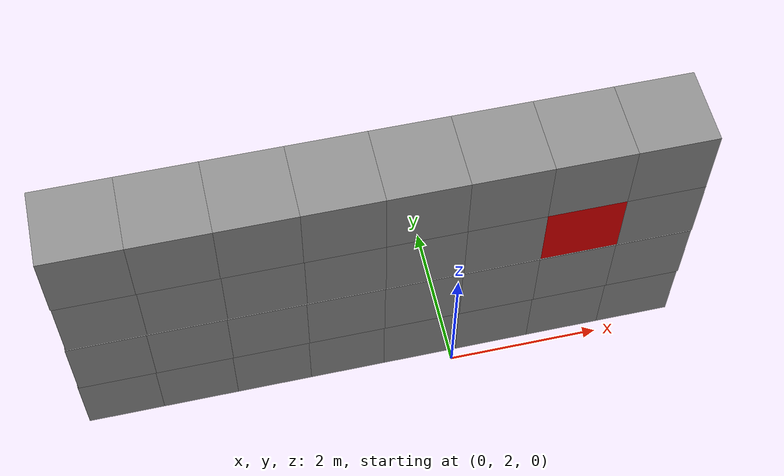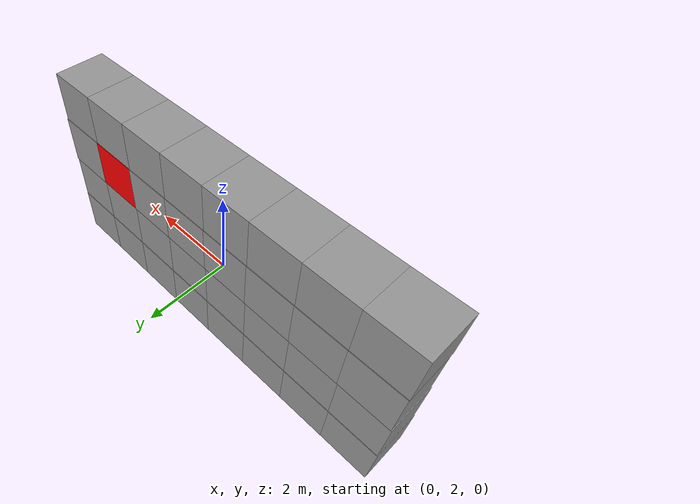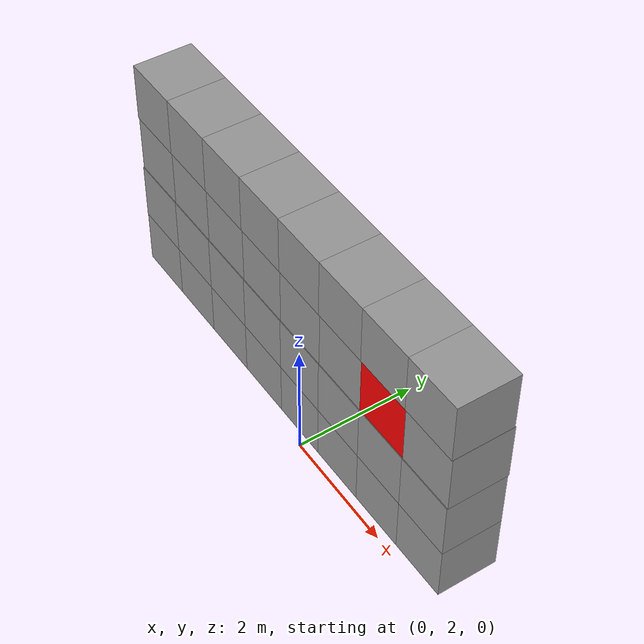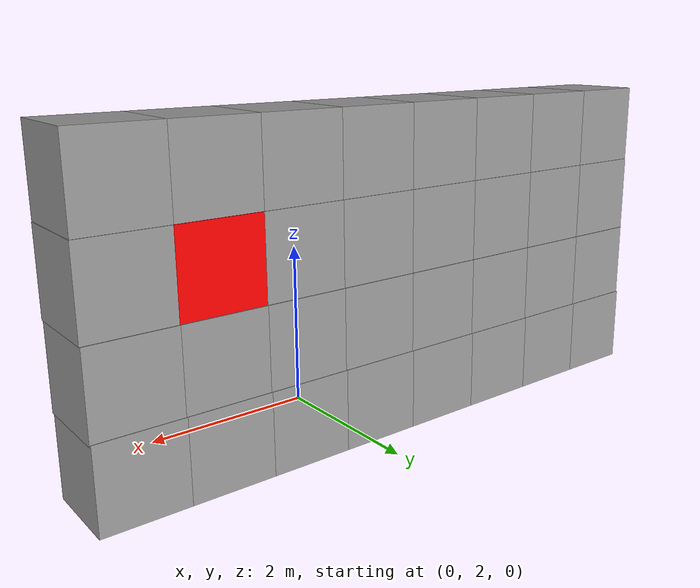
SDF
<sdf version="1.6">
 <world name="default">
  <light name="sun" type="directional">
   <pose>0 0 10 0 -0 0</pose>
   <diffuse>0.8 0.8 0.8 1</diffuse>
   <specular>0.2 0.2 0.2 1</specular>
   <attenuation>
    <range>1000</range>
    <constant>0.9</constant>
    <linear>0.01</linear>
    <quadratic>0.001</quadratic>
   </attenuation>
   <direction>-0.5 0.1 -0.9</direction>
  </light>
  <gravity>0 0 -9.8</gravity>
  <magnetic_field>6e-06 2.3e-05 -4.2e-05</magnetic_field>
  <atmosphere type="adiabatic"/>
  <physics name="default_physics" default="0" type="ode">
   <max_step_size>0.001</max_step_size>
   <real_time_factor>1</real_time_factor>
   <real_time_update_rate>1000</real_time_update_rate>
  </physics>
  <scene><ambient>0.4 0.4 0.4 1</ambient><background>0.7 0.7 0.7 1</background><shadows>1</shadows></scene>
  <spherical_coordinates>
   <surface_model>EARTH_WGS84</surface_model>
   <latitude_deg>0</latitude_deg>
   <longitude_deg>0</longitude_deg>
   <elevation>0</elevation>
   <heading_deg>0</heading_deg>
  </spherical_coordinates>
  <model name="ground_plane">
   <static>1</static>
   <link name="link">
    <collision name="collision">
     <geometry><plane><normal>0 0 1</normal><size>100 100</size></plane></geometry>
     <surface><friction><ode><mu>100</mu><mu2>50</mu2></ode></friction></surface>
    </collision>
   </link>
  </model>
  <model name="serial_blocks_wall">
   <model name="seiral_blocks">
    <link name="link_10">
     <pose>2.5 0 0 0 -0 0</pose>
     <inertial>
      <mass>1</mass>
      <inertia>
       <ixx>0.166667</ixx>
       <ixy>0</ixy>
       <ixz>0</ixz>
       <iyy>0.166667</iyy>
       <iyz>0</iyz>
       <izz>0.166667</izz>
      </inertia>
     </inertial>
     <visual name="visual">
      <geometry><box><size>1 1 1</size></box></geometry>
      <material>
       <lighting>1</lighting>
       <script><uri>file://media/materials/scripts/gazebo.material</uri><name>Gazebo/Grey</name></script>
       <shader type="pixel"><normal_map>__default__</normal_map></shader>
       <ambient>0.3 0.3 0.3 1</ambient>
       <diffuse>0.7 0.7 0.7 1</diffuse>
       <specular>0.01 0.01 0.01 1</specular>
       <emissive>0 0 0 1</emissive>
      </material>
     </visual>
     <collision name="collision">
      <geometry><box><size>1 1 1</size></box></geometry>
      <surface>
       <friction>
        <ode><mu>1</mu><mu2>1</mu2><fdir1>0 0 0</fdir1><slip1>0</slip1><slip2>0</slip2></ode>
        <torsional>
         <coefficient>1</coefficient>
         <patch_radius>0</patch_radius>
         <surface_radius>0</surface_radius>
         <use_patch_radius>1</use_patch_radius>
         <ode><slip>0</slip></ode>
        </torsional>
       </friction>
       <bounce><restitution_coefficient>0</restitution_coefficient><threshold>1e+06</threshold></bounce>
       <contact>
        <collide_without_contact>0</collide_without_contact>
        <collide_without_contact_bitmask>1</collide_without_contact_bitmask>
        <collide_bitmask>1</collide_bitmask>
        <ode>
         <soft_cfm>0</soft_cfm>
         <soft_erp>0.2</soft_erp>
         <kp>1e+13</kp>
         <kd>1</kd>
         <max_vel>0.01</max_vel>
         <min_depth>0</min_depth>
        </ode>
        <bullet>
         <split_impulse>1</split_impulse>
         <split_impulse_penetration_threshold>-0.01</split_impulse_penetration_threshold>
         <soft_cfm>0</soft_cfm>
         <soft_erp>0.2</soft_erp>
         <kp>1e+13</kp>
         <kd>1</kd>
        </bullet>
       </contact>
      </surface>
     </collision>
    </link>
    <link name="link_11">
     <pose>3.5 0 0 0 -0 0</pose>
     <inertial>
      <mass>1</mass>
      <inertia>
       <ixx>0.166667</ixx>
       <ixy>0</ixy>
       <ixz>0</ixz>
       <iyy>0.166667</iyy>
       <iyz>0</iyz>
       <izz>0.166667</izz>
      </inertia>
     </inertial>
     <visual name="visual">
      <geometry><box><size>1 1 1</size></box></geometry>
      <material>
       <lighting>1</lighting>
       <script><uri>file://media/materials/scripts/gazebo.material</uri><name>Gazebo/Grey</name></script>
       <shader type="pixel"><normal_map>__default__</normal_map></shader>
       <ambient>0.3 0.3 0.3 1</ambient>
       <diffuse>0.7 0.7 0.7 1</diffuse>
       <specular>0.01 0.01 0.01 1</specular>
       <emissive>0 0 0 1</emissive>
      </material>
     </visual>
     <collision name="collision">
      <geometry><box><size>1 1 1</size></box></geometry>
      <surface>
       <friction>
        <ode><mu>1</mu><mu2>1</mu2><fdir1>0 0 0</fdir1><slip1>0</slip1><slip2>0</slip2></ode>
        <torsional>
         <coefficient>1</coefficient>
         <patch_radius>0</patch_radius>
         <surface_radius>0</surface_radius>
         <use_patch_radius>1</use_patch_radius>
         <ode><slip>0</slip></ode>
        </torsional>
       </friction>
       <bounce><restitution_coefficient>0</restitution_coefficient><threshold>1e+06</threshold></bounce>
       <contact>
        <collide_without_contact>0</collide_without_contact>
        <collide_without_contact_bitmask>1</collide_without_contact_bitmask>
        <collide_bitmask>1</collide_bitmask>
        <ode>
         <soft_cfm>0</soft_cfm>
         <soft_erp>0.2</soft_erp>
         <kp>1e+13</kp>
         <kd>1</kd>
         <max_vel>0.01</max_vel>
         <min_depth>0</min_depth>
        </ode>
        <bullet>
         <split_impulse>1</split_impulse>
         <split_impulse_penetration_threshold>-0.01</split_impulse_penetration_threshold>
         <soft_cfm>0</soft_cfm>
         <soft_erp>0.2</soft_erp>
         <kp>1e+13</kp>
         <kd>1</kd>
        </bullet>
       </contact>
      </surface>
     </collision>
    </link>
    <link name="link_15">
     <pose>-2.5 0 0 0 -0 0</pose>
     <inertial>
      <mass>1</mass>
      <inertia>
       <ixx>0.166667</ixx>
       <ixy>0</ixy>
       <ixz>0</ixz>
       <iyy>0.166667</iyy>
       <iyz>0</iyz>
       <izz>0.166667</izz>
      </inertia>
     </inertial>
     <visual name="visual">
      <geometry><box><size>1 1 1</size></box></geometry>
      <material>
       <lighting>1</lighting>
       <script><uri>file://media/materials/scripts/gazebo.material</uri><name>Gazebo/Grey</name></script>
       <shader type="pixel"><normal_map>__default__</normal_map></shader>
       <ambient>0.3 0.3 0.3 1</ambient>
       <diffuse>0.7 0.7 0.7 1</diffuse>
       <specular>0.01 0.01 0.01 1</specular>
       <emissive>0 0 0 1</emissive>
      </material>
     </visual>
     <collision name="collision">
      <geometry><box><size>1 1 1</size></box></geometry>
      <surface>
       <friction>
        <ode><mu>1</mu><mu2>1</mu2><fdir1>0 0 0</fdir1><slip1>0</slip1><slip2>0</slip2></ode>
        <torsional>
         <coefficient>1</coefficient>
         <patch_radius>0</patch_radius>
         <surface_radius>0</surface_radius>
         <use_patch_radius>1</use_patch_radius>
         <ode><slip>0</slip></ode>
        </torsional>
       </friction>
       <bounce><restitution_coefficient>0</restitution_coefficient><threshold>1e+06</threshold></bounce>
       <contact>
        <collide_without_contact>0</collide_without_contact>
        <collide_without_contact_bitmask>1</collide_without_contact_bitmask>
        <collide_bitmask>1</collide_bitmask>
        <ode>
         <soft_cfm>0</soft_cfm>
         <soft_erp>0.2</soft_erp>
         <kp>1e+13</kp>
         <kd>1</kd>
         <max_vel>0.01</max_vel>
         <min_depth>0</min_depth>
        </ode>
        <bullet>
         <split_impulse>1</split_impulse>
         <split_impulse_penetration_threshold>-0.01</split_impulse_penetration_threshold>
         <soft_cfm>0</soft_cfm>
         <soft_erp>0.2</soft_erp>
         <kp>1e+13</kp>
         <kd>1</kd>
        </bullet>
       </contact>
      </surface>
     </collision>
    </link>
    <link name="link_16">
     <pose>-0.5 0 0 0 -0 0</pose>
     <inertial>
      <mass>1</mass>
      <inertia>
       <ixx>0.166667</ixx>
       <ixy>0</ixy>
       <ixz>0</ixz>
       <iyy>0.166667</iyy>
       <iyz>0</iyz>
       <izz>0.166667</izz>
      </inertia>
     </inertial>
     <visual name="visual">
      <geometry><box><size>1 1 1</size></box></geometry>
      <material>
       <lighting>1</lighting>
       <script><uri>file://media/materials/scripts/gazebo.material</uri><name>Gazebo/Grey</name></script>
       <shader type="pixel"><normal_map>__default__</normal_map></shader>
       <ambient>0.3 0.3 0.3 1</ambient>
       <diffuse>0.7 0.7 0.7 1</diffuse>
       <specular>0.01 0.01 0.01 1</specular>
       <emissive>0 0 0 1</emissive>
      </material>
     </visual>
     <collision name="collision">
      <geometry><box><size>1 1 1</size></box></geometry>
      <surface>
       <friction>
        <ode><mu>1</mu><mu2>1</mu2><fdir1>0 0 0</fdir1><slip1>0</slip1><slip2>0</slip2></ode>
        <torsional>
         <coefficient>1</coefficient>
         <patch_radius>0</patch_radius>
         <surface_radius>0</surface_radius>
         <use_patch_radius>1</use_patch_radius>
         <ode><slip>0</slip></ode>
        </torsional>
       </friction>
       <bounce><restitution_coefficient>0</restitution_coefficient><threshold>1e+06</threshold></bounce>
       <contact>
        <collide_without_contact>0</collide_without_contact>
        <collide_without_contact_bitmask>1</collide_without_contact_bitmask>
        <collide_bitmask>1</collide_bitmask>
        <ode>
         <soft_cfm>0</soft_cfm>
         <soft_erp>0.2</soft_erp>
         <kp>1e+13</kp>
         <kd>1</kd>
         <max_vel>0.01</max_vel>
         <min_depth>0</min_depth>
        </ode>
        <bullet>
         <split_impulse>1</split_impulse>
         <split_impulse_penetration_threshold>-0.01</split_impulse_penetration_threshold>
         <soft_cfm>0</soft_cfm>
         <soft_erp>0.2</soft_erp>
         <kp>1e+13</kp>
         <kd>1</kd>
        </bullet>
       </contact>
      </surface>
     </collision>
    </link>
    <link name="link_6">
     <pose>-1.5 0 0 0 -0 0</pose>
     <inertial>
      <mass>1</mass>
      <inertia>
       <ixx>0.166667</ixx>
       <ixy>0</ixy>
       <ixz>0</ixz>
       <iyy>0.166667</iyy>
       <iyz>0</iyz>
       <izz>0.166667</izz>
      </inertia>
     </inertial>
     <visual name="visual">
      <geometry><box><size>1 1 1</size></box></geometry>
      <material>
       <lighting>1</lighting>
       <script><uri>file://media/materials/scripts/gazebo.material</uri><name>Gazebo/Grey</name></script>
       <shader type="pixel"><normal_map>__default__</normal_map></shader>
       <ambient>0.3 0.3 0.3 1</ambient>
       <diffuse>0.7 0.7 0.7 1</diffuse>
       <specular>0.01 0.01 0.01 1</specular>
       <emissive>0 0 0 1</emissive>
      </material>
     </visual>
     <collision name="collision">
      <geometry><box><size>1 1 1</size></box></geometry>
      <surface>
       <friction>
        <ode><mu>1</mu><mu2>1</mu2><fdir1>0 0 0</fdir1><slip1>0</slip1><slip2>0</slip2></ode>
        <torsional>
         <coefficient>1</coefficient>
         <patch_radius>0</patch_radius>
         <surface_radius>0</surface_radius>
         <use_patch_radius>1</use_patch_radius>
         <ode><slip>0</slip></ode>
        </torsional>
       </friction>
       <bounce><restitution_coefficient>0</restitution_coefficient><threshold>1e+06</threshold></bounce>
       <contact>
        <collide_without_contact>0</collide_without_contact>
        <collide_without_contact_bitmask>1</collide_without_contact_bitmask>
        <collide_bitmask>1</collide_bitmask>
        <ode>
         <soft_cfm>0</soft_cfm>
         <soft_erp>0.2</soft_erp>
         <kp>1e+13</kp>
         <kd>1</kd>
         <max_vel>0.01</max_vel>
         <min_depth>0</min_depth>
        </ode>
        <bullet>
         <split_impulse>1</split_impulse>
         <split_impulse_penetration_threshold>-0.01</split_impulse_penetration_threshold>
         <soft_cfm>0</soft_cfm>
         <soft_erp>0.2</soft_erp>
         <kp>1e+13</kp>
         <kd>1</kd>
        </bullet>
       </contact>
      </surface>
     </collision>
    </link>
    <link name="link_7">
     <pose>-3.5 0 0 0 -0 0</pose>
     <inertial>
      <mass>1</mass>
      <inertia>
       <ixx>0.166667</ixx>
       <ixy>0</ixy>
       <ixz>0</ixz>
       <iyy>0.166667</iyy>
       <iyz>0</iyz>
       <izz>0.166667</izz>
      </inertia>
     </inertial>
     <visual name="visual">
      <geometry><box><size>1 1 1</size></box></geometry>
      <material>
       <lighting>1</lighting>
       <script><uri>file://media/materials/scripts/gazebo.material</uri><name>Gazebo/Grey</name></script>
       <shader type="pixel"><normal_map>__default__</normal_map></shader>
       <ambient>0.3 0.3 0.3 1</ambient>
       <diffuse>0.7 0.7 0.7 1</diffuse>
       <specular>0.01 0.01 0.01 1</specular>
       <emissive>0 0 0 1</emissive>
      </material>
     </visual>
     <collision name="collision">
      <geometry><box><size>1 1 1</size></box></geometry>
      <surface>
       <friction>
        <ode><mu>1</mu><mu2>1</mu2><fdir1>0 0 0</fdir1><slip1>0</slip1><slip2>0</slip2></ode>
        <torsional>
         <coefficient>1</coefficient>
         <patch_radius>0</patch_radius>
         <surface_radius>0</surface_radius>
         <use_patch_radius>1</use_patch_radius>
         <ode><slip>0</slip></ode>
        </torsional>
       </friction>
       <bounce><restitution_coefficient>0</restitution_coefficient><threshold>1e+06</threshold></bounce>
       <contact>
        <collide_without_contact>0</collide_without_contact>
        <collide_without_contact_bitmask>1</collide_without_contact_bitmask>
        <collide_bitmask>1</collide_bitmask>
        <ode>
         <soft_cfm>0</soft_cfm>
         <soft_erp>0.2</soft_erp>
         <kp>1e+13</kp>
         <kd>1</kd>
         <max_vel>0.01</max_vel>
         <min_depth>0</min_depth>
        </ode>
        <bullet>
         <split_impulse>1</split_impulse>
         <split_impulse_penetration_threshold>-0.01</split_impulse_penetration_threshold>
         <soft_cfm>0</soft_cfm>
         <soft_erp>0.2</soft_erp>
         <kp>1e+13</kp>
         <kd>1</kd>
        </bullet>
       </contact>
      </surface>
     </collision>
    </link>
    <link name="link_8">
     <pose>0.5 0 0 0 -0 0</pose>
     <inertial>
      <mass>1</mass>
      <inertia>
       <ixx>0.166667</ixx>
       <ixy>0</ixy>
       <ixz>0</ixz>
       <iyy>0.166667</iyy>
       <iyz>0</iyz>
       <izz>0.166667</izz>
      </inertia>
     </inertial>
     <visual name="visual">
      <geometry><box><size>1 1 1</size></box></geometry>
      <material>
       <lighting>1</lighting>
       <script><uri>file://media/materials/scripts/gazebo.material</uri><name>Gazebo/Grey</name></script>
       <shader type="pixel"><normal_map>__default__</normal_map></shader>
       <ambient>0.3 0.3 0.3 1</ambient>
       <diffuse>0.7 0.7 0.7 1</diffuse>
       <specular>0.01 0.01 0.01 1</specular>
       <emissive>0 0 0 1</emissive>
      </material>
     </visual>
     <collision name="collision">
      <geometry><box><size>1 1 1</size></box></geometry>
      <surface>
       <friction>
        <ode><mu>1</mu><mu2>1</mu2><fdir1>0 0 0</fdir1><slip1>0</slip1><slip2>0</slip2></ode>
        <torsional>
         <coefficient>1</coefficient>
         <patch_radius>0</patch_radius>
         <surface_radius>0</surface_radius>
         <use_patch_radius>1</use_patch_radius>
         <ode><slip>0</slip></ode>
        </torsional>
       </friction>
       <bounce><restitution_coefficient>0</restitution_coefficient><threshold>1e+06</threshold></bounce>
       <contact>
        <collide_without_contact>0</collide_without_contact>
        <collide_without_contact_bitmask>1</collide_without_contact_bitmask>
        <collide_bitmask>1</collide_bitmask>
        <ode>
         <soft_cfm>0</soft_cfm>
         <soft_erp>0.2</soft_erp>
         <kp>1e+13</kp>
         <kd>1</kd>
         <max_vel>0.01</max_vel>
         <min_depth>0</min_depth>
        </ode>
        <bullet>
         <split_impulse>1</split_impulse>
         <split_impulse_penetration_threshold>-0.01</split_impulse_penetration_threshold>
         <soft_cfm>0</soft_cfm>
         <soft_erp>0.2</soft_erp>
         <kp>1e+13</kp>
         <kd>1</kd>
        </bullet>
       </contact>
      </surface>
     </collision>
    </link>
    <link name="link_9">
     <pose>1.5 0 0 0 -0 0</pose>
     <inertial>
      <mass>1</mass>
      <inertia>
       <ixx>0.166667</ixx>
       <ixy>0</ixy>
       <ixz>0</ixz>
       <iyy>0.166667</iyy>
       <iyz>0</iyz>
       <izz>0.166667</izz>
      </inertia>
     </inertial>
     <visual name="visual">
      <geometry><box><size>1 1 1</size></box></geometry>
      <material>
       <lighting>1</lighting>
       <script><uri>file://media/materials/scripts/gazebo.material</uri><name>Gazebo/Grey</name></script>
       <shader type="pixel"><normal_map>__default__</normal_map></shader>
       <ambient>0.3 0.3 0.3 1</ambient>
       <diffuse>0.7 0.7 0.7 1</diffuse>
       <specular>0.01 0.01 0.01 1</specular>
       <emissive>0 0 0 1</emissive>
      </material>
     </visual>
     <collision name="collision">
      <geometry><box><size>1 1 1</size></box></geometry>
      <surface>
       <friction>
        <ode><mu>1</mu><mu2>1</mu2><fdir1>0 0 0</fdir1><slip1>0</slip1><slip2>0</slip2></ode>
        <torsional>
         <coefficient>1</coefficient>
         <patch_radius>0</patch_radius>
         <surface_radius>0</surface_radius>
         <use_patch_radius>1</use_patch_radius>
         <ode><slip>0</slip></ode>
        </torsional>
       </friction>
       <bounce><restitution_coefficient>0</restitution_coefficient><threshold>1e+06</threshold></bounce>
       <contact>
        <collide_without_contact>0</collide_without_contact>
        <collide_without_contact_bitmask>1</collide_without_contact_bitmask>
        <collide_bitmask>1</collide_bitmask>
        <ode>
         <soft_cfm>0</soft_cfm>
         <soft_erp>0.2</soft_erp>
         <kp>1e+13</kp>
         <kd>1</kd>
         <max_vel>0.01</max_vel>
         <min_depth>0</min_depth>
        </ode>
        <bullet>
         <split_impulse>1</split_impulse>
         <split_impulse_penetration_threshold>-0.01</split_impulse_penetration_threshold>
         <soft_cfm>0</soft_cfm>
         <soft_erp>0.2</soft_erp>
         <kp>1e+13</kp>
         <kd>1</kd>
        </bullet>
       </contact>
      </surface>
     </collision>
    </link>
    <joint name="link_10_JOINT_10" type="fixed">
     <parent>link_10</parent>
     <child>link_11</child>
     <physics>
      <ode><limit><cfm>0</cfm><erp>0.2</erp></limit><suspension><cfm>0</cfm><erp>0.2</erp></suspension></ode>
     </physics>
    </joint>
    <joint name="link_15_JOINT_5" type="fixed">
     <parent>link_15</parent>
     <child>link_6</child>
     <physics>
      <ode><limit><cfm>0</cfm><erp>0.2</erp></limit><suspension><cfm>0</cfm><erp>0.2</erp></suspension></ode>
     </physics>
    </joint>
    <joint name="link_16_JOINT_7" type="fixed">
     <parent>link_16</parent>
     <child>link_8</child>
     <physics>
      <ode><limit><cfm>0</cfm><erp>0.2</erp></limit><suspension><cfm>0</cfm><erp>0.2</erp></suspension></ode>
     </physics>
    </joint>
    <joint name="link_6_JOINT_6" type="fixed">
     <parent>link_6</parent>
     <child>link_16</child>
     <physics>
      <ode><limit><cfm>0</cfm><erp>0.2</erp></limit><suspension><cfm>0</cfm><erp>0.2</erp></suspension></ode>
     </physics>
    </joint>
    <joint name="link_7_JOINT_4" type="fixed">
     <parent>link_7</parent>
     <child>link_15</child>
     <physics>
      <ode><limit><cfm>0</cfm><erp>0.2</erp></limit><suspension><cfm>0</cfm><erp>0.2</erp></suspension></ode>
     </physics>
    </joint>
    <joint name="link_8_JOINT_8" type="fixed">
     <parent>link_8</parent>
     <child>link_9</child>
     <physics>
      <ode><limit><cfm>0</cfm><erp>0.2</erp></limit><suspension><cfm>0</cfm><erp>0.2</erp></suspension></ode>
     </physics>
    </joint>
    <joint name="link_9_JOINT_9" type="fixed">
     <parent>link_9</parent>
     <child>link_10</child>
     <physics>
      <ode><limit><cfm>0</cfm><erp>0.2</erp></limit><suspension><cfm>0</cfm><erp>0.2</erp></suspension></ode>
     </physics>
    </joint>
    <static>0</static>
    <pose>-0.011667 0.005415 -1.48703 0 -0 0</pose>
   </model>
   <model name="seiral_blocks_0">
    <link name="link_10">
     <pose>2.5 0 0 0 -0 0</pose>
     <inertial>
      <mass>1</mass>
      <inertia>
       <ixx>0.166667</ixx>
       <ixy>0</ixy>
       <ixz>0</ixz>
       <iyy>0.166667</iyy>
       <iyz>0</iyz>
       <izz>0.166667</izz>
      </inertia>
     </inertial>
     <visual name="visual">
      <geometry><box><size>1 1 1</size></box></geometry>
      <material>
       <lighting>1</lighting>
       <script><uri>file://media/materials/scripts/gazebo.material</uri><name>Gazebo/Grey</name></script>
       <shader type="pixel"><normal_map>__default__</normal_map></shader>
       <ambient>0.3 0.3 0.3 1</ambient>
       <diffuse>0.7 0.7 0.7 1</diffuse>
       <specular>0.01 0.01 0.01 1</specular>
       <emissive>0 0 0 1</emissive>
      </material>
     </visual>
     <collision name="collision">
      <geometry><box><size>1 1 1</size></box></geometry>
      <surface>
       <friction>
        <ode><mu>1</mu><mu2>1</mu2><fdir1>0 0 0</fdir1><slip1>0</slip1><slip2>0</slip2></ode>
        <torsional>
         <coefficient>1</coefficient>
         <patch_radius>0</patch_radius>
         <surface_radius>0</surface_radius>
         <use_patch_radius>1</use_patch_radius>
         <ode><slip>0</slip></ode>
        </torsional>
       </friction>
       <bounce><restitution_coefficient>0</restitution_coefficient><threshold>1e+06</threshold></bounce>
       <contact>
        <collide_without_contact>0</collide_without_contact>
        <collide_without_contact_bitmask>1</collide_without_contact_bitmask>
        <collide_bitmask>1</collide_bitmask>
        <ode>
         <soft_cfm>0</soft_cfm>
         <soft_erp>0.2</soft_erp>
         <kp>1e+13</kp>
         <kd>1</kd>
         <max_vel>0.01</max_vel>
         <min_depth>0</min_depth>
        </ode>
        <bullet>
         <split_impulse>1</split_impulse>
         <split_impulse_penetration_threshold>-0.01</split_impulse_penetration_threshold>
         <soft_cfm>0</soft_cfm>
         <soft_erp>0.2</soft_erp>
         <kp>1e+13</kp>
         <kd>1</kd>
        </bullet>
       </contact>
      </surface>
     </collision>
    </link>
    <link name="link_11">
     <pose>3.5 0 0 0 -0 0</pose>
     <inertial>
      <mass>1</mass>
      <inertia>
       <ixx>0.166667</ixx>
       <ixy>0</ixy>
       <ixz>0</ixz>
       <iyy>0.166667</iyy>
       <iyz>0</iyz>
       <izz>0.166667</izz>
      </inertia>
     </inertial>
     <visual name="visual">
      <geometry><box><size>1 1 1</size></box></geometry>
      <material>
       <lighting>1</lighting>
       <script><uri>file://media/materials/scripts/gazebo.material</uri><name>Gazebo/Grey</name></script>
       <shader type="pixel"><normal_map>__default__</normal_map></shader>
       <ambient>0.3 0.3 0.3 1</ambient>
       <diffuse>0.7 0.7 0.7 1</diffuse>
       <specular>0.01 0.01 0.01 1</specular>
       <emissive>0 0 0 1</emissive>
      </material>
     </visual>
     <collision name="collision">
      <geometry><box><size>1 1 1</size></box></geometry>
      <surface>
       <friction>
        <ode><mu>1</mu><mu2>1</mu2><fdir1>0 0 0</fdir1><slip1>0</slip1><slip2>0</slip2></ode>
        <torsional>
         <coefficient>1</coefficient>
         <patch_radius>0</patch_radius>
         <surface_radius>0</surface_radius>
         <use_patch_radius>1</use_patch_radius>
         <ode><slip>0</slip></ode>
        </torsional>
       </friction>
       <bounce><restitution_coefficient>0</restitution_coefficient><threshold>1e+06</threshold></bounce>
       <contact>
        <collide_without_contact>0</collide_without_contact>
        <collide_without_contact_bitmask>1</collide_without_contact_bitmask>
        <collide_bitmask>1</collide_bitmask>
        <ode>
         <soft_cfm>0</soft_cfm>
         <soft_erp>0.2</soft_erp>
         <kp>1e+13</kp>
         <kd>1</kd>
         <max_vel>0.01</max_vel>
         <min_depth>0</min_depth>
        </ode>
        <bullet>
         <split_impulse>1</split_impulse>
         <split_impulse_penetration_threshold>-0.01</split_impulse_penetration_threshold>
         <soft_cfm>0</soft_cfm>
         <soft_erp>0.2</soft_erp>
         <kp>1e+13</kp>
         <kd>1</kd>
        </bullet>
       </contact>
      </surface>
     </collision>
    </link>
    <link name="link_15">
     <pose>-2.5 0 0 0 -0 0</pose>
     <inertial>
      <mass>1</mass>
      <inertia>
       <ixx>0.166667</ixx>
       <ixy>0</ixy>
       <ixz>0</ixz>
       <iyy>0.166667</iyy>
       <iyz>0</iyz>
       <izz>0.166667</izz>
      </inertia>
     </inertial>
     <visual name="visual">
      <geometry><box><size>1 1 1</size></box></geometry>
      <material>
       <lighting>1</lighting>
       <script><uri>file://media/materials/scripts/gazebo.material</uri><name>Gazebo/Grey</name></script>
       <shader type="pixel"><normal_map>__default__</normal_map></shader>
       <ambient>0.3 0.3 0.3 1</ambient>
       <diffuse>0.7 0.7 0.7 1</diffuse>
       <specular>0.01 0.01 0.01 1</specular>
       <emissive>0 0 0 1</emissive>
      </material>
     </visual>
     <collision name="collision">
      <geometry><box><size>1 1 1</size></box></geometry>
      <surface>
       <friction>
        <ode><mu>1</mu><mu2>1</mu2><fdir1>0 0 0</fdir1><slip1>0</slip1><slip2>0</slip2></ode>
        <torsional>
         <coefficient>1</coefficient>
         <patch_radius>0</patch_radius>
         <surface_radius>0</surface_radius>
         <use_patch_radius>1</use_patch_radius>
         <ode><slip>0</slip></ode>
        </torsional>
       </friction>
       <bounce><restitution_coefficient>0</restitution_coefficient><threshold>1e+06</threshold></bounce>
       <contact>
        <collide_without_contact>0</collide_without_contact>
        <collide_without_contact_bitmask>1</collide_without_contact_bitmask>
        <collide_bitmask>1</collide_bitmask>
        <ode>
         <soft_cfm>0</soft_cfm>
         <soft_erp>0.2</soft_erp>
         <kp>1e+13</kp>
         <kd>1</kd>
         <max_vel>0.01</max_vel>
         <min_depth>0</min_depth>
        </ode>
        <bullet>
         <split_impulse>1</split_impulse>
         <split_impulse_penetration_threshold>-0.01</split_impulse_penetration_threshold>
         <soft_cfm>0</soft_cfm>
         <soft_erp>0.2</soft_erp>
         <kp>1e+13</kp>
         <kd>1</kd>
        </bullet>
       </contact>
      </surface>
     </collision>
    </link>
    <link name="link_16">
     <pose>-0.5 0 0 0 -0 0</pose>
     <inertial>
      <mass>1</mass>
      <inertia>
       <ixx>0.166667</ixx>
       <ixy>0</ixy>
       <ixz>0</ixz>
       <iyy>0.166667</iyy>
       <iyz>0</iyz>
       <izz>0.166667</izz>
      </inertia>
     </inertial>
     <visual name="visual">
      <geometry><box><size>1 1 1</size></box></geometry>
      <material>
       <lighting>1</lighting>
       <script><uri>file://media/materials/scripts/gazebo.material</uri><name>Gazebo/Grey</name></script>
       <shader type="pixel"><normal_map>__default__</normal_map></shader>
       <ambient>0.3 0.3 0.3 1</ambient>
       <diffuse>0.7 0.7 0.7 1</diffuse>
       <specular>0.01 0.01 0.01 1</specular>
       <emissive>0 0 0 1</emissive>
      </material>
     </visual>
     <collision name="collision">
      <geometry><box><size>1 1 1</size></box></geometry>
      <surface>
       <friction>
        <ode><mu>1</mu><mu2>1</mu2><fdir1>0 0 0</fdir1><slip1>0</slip1><slip2>0</slip2></ode>
        <torsional>
         <coefficient>1</coefficient>
         <patch_radius>0</patch_radius>
         <surface_radius>0</surface_radius>
         <use_patch_radius>1</use_patch_radius>
         <ode><slip>0</slip></ode>
        </torsional>
       </friction>
       <bounce><restitution_coefficient>0</restitution_coefficient><threshold>1e+06</threshold></bounce>
       <contact>
        <collide_without_contact>0</collide_without_contact>
        <collide_without_contact_bitmask>1</collide_without_contact_bitmask>
        <collide_bitmask>1</collide_bitmask>
        <ode>
         <soft_cfm>0</soft_cfm>
         <soft_erp>0.2</soft_erp>
         <kp>1e+13</kp>
         <kd>1</kd>
         <max_vel>0.01</max_vel>
         <min_depth>0</min_depth>
        </ode>
        <bullet>
         <split_impulse>1</split_impulse>
         <split_impulse_penetration_threshold>-0.01</split_impulse_penetration_threshold>
         <soft_cfm>0</soft_cfm>
         <soft_erp>0.2</soft_erp>
         <kp>1e+13</kp>
         <kd>1</kd>
        </bullet>
       </contact>
      </surface>
     </collision>
    </link>
    <link name="link_6">
     <pose>-1.5 0 0 0 -0 0</pose>
     <inertial>
      <mass>1</mass>
      <inertia>
       <ixx>0.166667</ixx>
       <ixy>0</ixy>
       <ixz>0</ixz>
       <iyy>0.166667</iyy>
       <iyz>0</iyz>
       <izz>0.166667</izz>
      </inertia>
     </inertial>
     <visual name="visual">
      <geometry><box><size>1 1 1</size></box></geometry>
      <material>
       <lighting>1</lighting>
       <script><uri>file://media/materials/scripts/gazebo.material</uri><name>Gazebo/Grey</name></script>
       <shader type="pixel"><normal_map>__default__</normal_map></shader>
       <ambient>0.3 0.3 0.3 1</ambient>
       <diffuse>0.7 0.7 0.7 1</diffuse>
       <specular>0.01 0.01 0.01 1</specular>
       <emissive>0 0 0 1</emissive>
      </material>
     </visual>
     <collision name="collision">
      <geometry><box><size>1 1 1</size></box></geometry>
      <surface>
       <friction>
        <ode><mu>1</mu><mu2>1</mu2><fdir1>0 0 0</fdir1><slip1>0</slip1><slip2>0</slip2></ode>
        <torsional>
         <coefficient>1</coefficient>
         <patch_radius>0</patch_radius>
         <surface_radius>0</surface_radius>
         <use_patch_radius>1</use_patch_radius>
         <ode><slip>0</slip></ode>
        </torsional>
       </friction>
       <bounce><restitution_coefficient>0</restitution_coefficient><threshold>1e+06</threshold></bounce>
       <contact>
        <collide_without_contact>0</collide_without_contact>
        <collide_without_contact_bitmask>1</collide_without_contact_bitmask>
        <collide_bitmask>1</collide_bitmask>
        <ode>
         <soft_cfm>0</soft_cfm>
         <soft_erp>0.2</soft_erp>
         <kp>1e+13</kp>
         <kd>1</kd>
         <max_vel>0.01</max_vel>
         <min_depth>0</min_depth>
        </ode>
        <bullet>
         <split_impulse>1</split_impulse>
         <split_impulse_penetration_threshold>-0.01</split_impulse_penetration_threshold>
         <soft_cfm>0</soft_cfm>
         <soft_erp>0.2</soft_erp>
         <kp>1e+13</kp>
         <kd>1</kd>
        </bullet>
       </contact>
      </surface>
     </collision>
    </link>
    <link name="link_7">
     <pose>-3.5 0 0 0 -0 0</pose>
     <inertial>
      <mass>1</mass>
      <inertia>
       <ixx>0.166667</ixx>
       <ixy>0</ixy>
       <ixz>0</ixz>
       <iyy>0.166667</iyy>
       <iyz>0</iyz>
       <izz>0.166667</izz>
      </inertia>
     </inertial>
     <visual name="visual">
      <geometry><box><size>1 1 1</size></box></geometry>
      <material>
       <lighting>1</lighting>
       <script><uri>file://media/materials/scripts/gazebo.material</uri><name>Gazebo/Grey</name></script>
       <shader type="pixel"><normal_map>__default__</normal_map></shader>
       <ambient>0.3 0.3 0.3 1</ambient>
       <diffuse>0.7 0.7 0.7 1</diffuse>
       <specular>0.01 0.01 0.01 1</specular>
       <emissive>0 0 0 1</emissive>
      </material>
     </visual>
     <collision name="collision">
      <geometry><box><size>1 1 1</size></box></geometry>
      <surface>
       <friction>
        <ode><mu>1</mu><mu2>1</mu2><fdir1>0 0 0</fdir1><slip1>0</slip1><slip2>0</slip2></ode>
        <torsional>
         <coefficient>1</coefficient>
         <patch_radius>0</patch_radius>
         <surface_radius>0</surface_radius>
         <use_patch_radius>1</use_patch_radius>
         <ode><slip>0</slip></ode>
        </torsional>
       </friction>
       <bounce><restitution_coefficient>0</restitution_coefficient><threshold>1e+06</threshold></bounce>
       <contact>
        <collide_without_contact>0</collide_without_contact>
        <collide_without_contact_bitmask>1</collide_without_contact_bitmask>
        <collide_bitmask>1</collide_bitmask>
        <ode>
         <soft_cfm>0</soft_cfm>
         <soft_erp>0.2</soft_erp>
         <kp>1e+13</kp>
         <kd>1</kd>
         <max_vel>0.01</max_vel>
         <min_depth>0</min_depth>
        </ode>
        <bullet>
         <split_impulse>1</split_impulse>
         <split_impulse_penetration_threshold>-0.01</split_impulse_penetration_threshold>
         <soft_cfm>0</soft_cfm>
         <soft_erp>0.2</soft_erp>
         <kp>1e+13</kp>
         <kd>1</kd>
        </bullet>
       </contact>
      </surface>
     </collision>
    </link>
    <link name="link_8">
     <pose>0.5 0 0 0 -0 0</pose>
     <inertial>
      <mass>1</mass>
      <inertia>
       <ixx>0.166667</ixx>
       <ixy>0</ixy>
       <ixz>0</ixz>
       <iyy>0.166667</iyy>
       <iyz>0</iyz>
       <izz>0.166667</izz>
      </inertia>
     </inertial>
     <visual name="visual">
      <geometry><box><size>1 1 1</size></box></geometry>
      <material>
       <lighting>1</lighting>
       <script><uri>file://media/materials/scripts/gazebo.material</uri><name>Gazebo/Grey</name></script>
       <shader type="pixel"><normal_map>__default__</normal_map></shader>
       <ambient>0.3 0.3 0.3 1</ambient>
       <diffuse>0.7 0.7 0.7 1</diffuse>
       <specular>0.01 0.01 0.01 1</specular>
       <emissive>0 0 0 1</emissive>
      </material>
     </visual>
     <collision name="collision">
      <geometry><box><size>1 1 1</size></box></geometry>
      <surface>
       <friction>
        <ode><mu>1</mu><mu2>1</mu2><fdir1>0 0 0</fdir1><slip1>0</slip1><slip2>0</slip2></ode>
        <torsional>
         <coefficient>1</coefficient>
         <patch_radius>0</patch_radius>
         <surface_radius>0</surface_radius>
         <use_patch_radius>1</use_patch_radius>
         <ode><slip>0</slip></ode>
        </torsional>
       </friction>
       <bounce><restitution_coefficient>0</restitution_coefficient><threshold>1e+06</threshold></bounce>
       <contact>
        <collide_without_contact>0</collide_without_contact>
        <collide_without_contact_bitmask>1</collide_without_contact_bitmask>
        <collide_bitmask>1</collide_bitmask>
        <ode>
         <soft_cfm>0</soft_cfm>
         <soft_erp>0.2</soft_erp>
         <kp>1e+13</kp>
         <kd>1</kd>
         <max_vel>0.01</max_vel>
         <min_depth>0</min_depth>
        </ode>
        <bullet>
         <split_impulse>1</split_impulse>
         <split_impulse_penetration_threshold>-0.01</split_impulse_penetration_threshold>
         <soft_cfm>0</soft_cfm>
         <soft_erp>0.2</soft_erp>
         <kp>1e+13</kp>
         <kd>1</kd>
        </bullet>
       </contact>
      </surface>
     </collision>
    </link>
    <link name="link_9">
     <pose>1.5 0 0 0 -0 0</pose>
     <inertial>
      <mass>1</mass>
      <inertia>
       <ixx>0.166667</ixx>
       <ixy>0</ixy>
       <ixz>0</ixz>
       <iyy>0.166667</iyy>
       <iyz>0</iyz>
       <izz>0.166667</izz>
      </inertia>
     </inertial>
     <visual name="visual">
      <geometry><box><size>1 1 1</size></box></geometry>
      <material>
       <lighting>1</lighting>
       <script><uri>file://media/materials/scripts/gazebo.material</uri><name>Gazebo/Grey</name></script>
       <shader type="pixel"><normal_map>__default__</normal_map></shader>
       <ambient>0.3 0.3 0.3 1</ambient>
       <diffuse>0.7 0.7 0.7 1</diffuse>
       <specular>0.01 0.01 0.01 1</specular>
       <emissive>0 0 0 1</emissive>
      </material>
     </visual>
     <collision name="collision">
      <geometry><box><size>1 1 1</size></box></geometry>
      <surface>
       <friction>
        <ode><mu>1</mu><mu2>1</mu2><fdir1>0 0 0</fdir1><slip1>0</slip1><slip2>0</slip2></ode>
        <torsional>
         <coefficient>1</coefficient>
         <patch_radius>0</patch_radius>
         <surface_radius>0</surface_radius>
         <use_patch_radius>1</use_patch_radius>
         <ode><slip>0</slip></ode>
        </torsional>
       </friction>
       <bounce><restitution_coefficient>0</restitution_coefficient><threshold>1e+06</threshold></bounce>
       <contact>
        <collide_without_contact>0</collide_without_contact>
        <collide_without_contact_bitmask>1</collide_without_contact_bitmask>
        <collide_bitmask>1</collide_bitmask>
        <ode>
         <soft_cfm>0</soft_cfm>
         <soft_erp>0.2</soft_erp>
         <kp>1e+13</kp>
         <kd>1</kd>
         <max_vel>0.01</max_vel>
         <min_depth>0</min_depth>
        </ode>
        <bullet>
         <split_impulse>1</split_impulse>
         <split_impulse_penetration_threshold>-0.01</split_impulse_penetration_threshold>
         <soft_cfm>0</soft_cfm>
         <soft_erp>0.2</soft_erp>
         <kp>1e+13</kp>
         <kd>1</kd>
        </bullet>
       </contact>
      </surface>
     </collision>
    </link>
    <joint name="link_10_JOINT_10" type="fixed">
     <parent>link_10</parent>
     <child>link_11</child>
     <physics>
      <ode><limit><cfm>0</cfm><erp>0.2</erp></limit><suspension><cfm>0</cfm><erp>0.2</erp></suspension></ode>
     </physics>
    </joint>
    <joint name="link_15_JOINT_5" type="fixed">
     <parent>link_15</parent>
     <child>link_6</child>
     <physics>
      <ode><limit><cfm>0</cfm><erp>0.2</erp></limit><suspension><cfm>0</cfm><erp>0.2</erp></suspension></ode>
     </physics>
    </joint>
    <joint name="link_16_JOINT_7" type="fixed">
     <parent>link_16</parent>
     <child>link_8</child>
     <physics>
      <ode><limit><cfm>0</cfm><erp>0.2</erp></limit><suspension><cfm>0</cfm><erp>0.2</erp></suspension></ode>
     </physics>
    </joint>
    <joint name="link_6_JOINT_6" type="fixed">
     <parent>link_6</parent>
     <child>link_16</child>
     <physics>
      <ode><limit><cfm>0</cfm><erp>0.2</erp></limit><suspension><cfm>0</cfm><erp>0.2</erp></suspension></ode>
     </physics>
    </joint>
    <joint name="link_7_JOINT_4" type="fixed">
     <parent>link_7</parent>
     <child>link_15</child>
     <physics>
      <ode><limit><cfm>0</cfm><erp>0.2</erp></limit><suspension><cfm>0</cfm><erp>0.2</erp></suspension></ode>
     </physics>
    </joint>
    <joint name="link_8_JOINT_8" type="fixed">
     <parent>link_8</parent>
     <child>link_9</child>
     <physics>
      <ode><limit><cfm>0</cfm><erp>0.2</erp></limit><suspension><cfm>0</cfm><erp>0.2</erp></suspension></ode>
     </physics>
    </joint>
    <joint name="link_9_JOINT_9" type="fixed">
     <parent>link_9</parent>
     <child>link_10</child>
     <physics>
      <ode><limit><cfm>0</cfm><erp>0.2</erp></limit><suspension><cfm>0</cfm><erp>0.2</erp></suspension></ode>
     </physics>
    </joint>
    <static>0</static>
    <pose>-0.001907 -0.002948 -0.508385 0 -0 0</pose>
   </model>
   <model name="seiral_blocks_1">
    <link name="link_10">
     <pose>2.5 0 0 0 -0 0</pose>
     <inertial>
      <mass>1</mass>
      <inertia>
       <ixx>0.166667</ixx>
       <ixy>0</ixy>
       <ixz>0</ixz>
       <iyy>0.166667</iyy>
       <iyz>0</iyz>
       <izz>0.166667</izz>
      </inertia>
     </inertial>
     <visual name="visual">
      <geometry><box><size>1 1 1</size></box></geometry>
      <material>
       <lighting>1</lighting>
       <script><uri>file://media/materials/scripts/gazebo.material</uri><name>Gazebo/Grey</name></script>
       <shader type="pixel"><normal_map>__default__</normal_map></shader>
       <ambient>0.3 0.3 0.3 1</ambient>
       <diffuse>0.7 0.7 0.7 1</diffuse>
       <specular>0.01 0.01 0.01 1</specular>
       <emissive>0 0 0 1</emissive>
      </material>
     </visual>
     <collision name="collision">
      <geometry><box><size>1 1 1</size></box></geometry>
      <surface>
       <friction>
        <ode><mu>1</mu><mu2>1</mu2><fdir1>0 0 0</fdir1><slip1>0</slip1><slip2>0</slip2></ode>
        <torsional>
         <coefficient>1</coefficient>
         <patch_radius>0</patch_radius>
         <surface_radius>0</surface_radius>
         <use_patch_radius>1</use_patch_radius>
         <ode><slip>0</slip></ode>
        </torsional>
       </friction>
       <bounce><restitution_coefficient>0</restitution_coefficient><threshold>1e+06</threshold></bounce>
       <contact>
        <collide_without_contact>0</collide_without_contact>
        <collide_without_contact_bitmask>1</collide_without_contact_bitmask>
        <collide_bitmask>1</collide_bitmask>
        <ode>
         <soft_cfm>0</soft_cfm>
         <soft_erp>0.2</soft_erp>
         <kp>1e+13</kp>
         <kd>1</kd>
         <max_vel>0.01</max_vel>
         <min_depth>0</min_depth>
        </ode>
        <bullet>
         <split_impulse>1</split_impulse>
         <split_impulse_penetration_threshold>-0.01</split_impulse_penetration_threshold>
         <soft_cfm>0</soft_cfm>
         <soft_erp>0.2</soft_erp>
         <kp>1e+13</kp>
         <kd>1</kd>
        </bullet>
       </contact>
      </surface>
     </collision>
    </link>
    <link name="link_11">
     <pose>3.5 0 0 0 -0 0</pose>
     <inertial>
      <mass>1</mass>
      <inertia>
       <ixx>0.166667</ixx>
       <ixy>0</ixy>
       <ixz>0</ixz>
       <iyy>0.166667</iyy>
       <iyz>0</iyz>
       <izz>0.166667</izz>
      </inertia>
     </inertial>
     <visual name="visual">
      <geometry><box><size>1 1 1</size></box></geometry>
      <material>
       <lighting>1</lighting>
       <script><uri>file://media/materials/scripts/gazebo.material</uri><name>Gazebo/Grey</name></script>
       <shader type="pixel"><normal_map>__default__</normal_map></shader>
       <ambient>0.3 0.3 0.3 1</ambient>
       <diffuse>0.7 0.7 0.7 1</diffuse>
       <specular>0.01 0.01 0.01 1</specular>
       <emissive>0 0 0 1</emissive>
      </material>
     </visual>
     <collision name="collision">
      <geometry><box><size>1 1 1</size></box></geometry>
      <surface>
       <friction>
        <ode><mu>1</mu><mu2>1</mu2><fdir1>0 0 0</fdir1><slip1>0</slip1><slip2>0</slip2></ode>
        <torsional>
         <coefficient>1</coefficient>
         <patch_radius>0</patch_radius>
         <surface_radius>0</surface_radius>
         <use_patch_radius>1</use_patch_radius>
         <ode><slip>0</slip></ode>
        </torsional>
       </friction>
       <bounce><restitution_coefficient>0</restitution_coefficient><threshold>1e+06</threshold></bounce>
       <contact>
        <collide_without_contact>0</collide_without_contact>
        <collide_without_contact_bitmask>1</collide_without_contact_bitmask>
        <collide_bitmask>1</collide_bitmask>
        <ode>
         <soft_cfm>0</soft_cfm>
         <soft_erp>0.2</soft_erp>
         <kp>1e+13</kp>
         <kd>1</kd>
         <max_vel>0.01</max_vel>
         <min_depth>0</min_depth>
        </ode>
        <bullet>
         <split_impulse>1</split_impulse>
         <split_impulse_penetration_threshold>-0.01</split_impulse_penetration_threshold>
         <soft_cfm>0</soft_cfm>
         <soft_erp>0.2</soft_erp>
         <kp>1e+13</kp>
         <kd>1</kd>
        </bullet>
       </contact>
      </surface>
     </collision>
    </link>
    <link name="link_15">
     <pose>-2.5 0 0 0 -0 0</pose>
     <inertial>
      <mass>1</mass>
      <inertia>
       <ixx>0.166667</ixx>
       <ixy>0</ixy>
       <ixz>0</ixz>
       <iyy>0.166667</iyy>
       <iyz>0</iyz>
       <izz>0.166667</izz>
      </inertia>
     </inertial>
     <visual name="visual">
      <geometry><box><size>1 1 1</size></box></geometry>
      <material>
       <lighting>1</lighting>
       <script><uri>file://media/materials/scripts/gazebo.material</uri><name>Gazebo/Grey</name></script>
       <shader type="pixel"><normal_map>__default__</normal_map></shader>
       <ambient>0.3 0.3 0.3 1</ambient>
       <diffuse>0.7 0.7 0.7 1</diffuse>
       <specular>0.01 0.01 0.01 1</specular>
       <emissive>0 0 0 1</emissive>
      </material>
     </visual>
     <collision name="collision">
      <geometry><box><size>1 1 1</size></box></geometry>
      <surface>
       <friction>
        <ode><mu>1</mu><mu2>1</mu2><fdir1>0 0 0</fdir1><slip1>0</slip1><slip2>0</slip2></ode>
        <torsional>
         <coefficient>1</coefficient>
         <patch_radius>0</patch_radius>
         <surface_radius>0</surface_radius>
         <use_patch_radius>1</use_patch_radius>
         <ode><slip>0</slip></ode>
        </torsional>
       </friction>
       <bounce><restitution_coefficient>0</restitution_coefficient><threshold>1e+06</threshold></bounce>
       <contact>
        <collide_without_contact>0</collide_without_contact>
        <collide_without_contact_bitmask>1</collide_without_contact_bitmask>
        <collide_bitmask>1</collide_bitmask>
        <ode>
         <soft_cfm>0</soft_cfm>
         <soft_erp>0.2</soft_erp>
         <kp>1e+13</kp>
         <kd>1</kd>
         <max_vel>0.01</max_vel>
         <min_depth>0</min_depth>
        </ode>
        <bullet>
         <split_impulse>1</split_impulse>
         <split_impulse_penetration_threshold>-0.01</split_impulse_penetration_threshold>
         <soft_cfm>0</soft_cfm>
         <soft_erp>0.2</soft_erp>
         <kp>1e+13</kp>
         <kd>1</kd>
        </bullet>
       </contact>
      </surface>
     </collision>
    </link>
    <link name="link_16">
     <pose>-0.5 0 0 0 -0 0</pose>
     <inertial>
      <mass>1</mass>
      <inertia>
       <ixx>0.166667</ixx>
       <ixy>0</ixy>
       <ixz>0</ixz>
       <iyy>0.166667</iyy>
       <iyz>0</iyz>
       <izz>0.166667</izz>
      </inertia>
     </inertial>
     <visual name="visual">
      <geometry><box><size>1 1 1</size></box></geometry>
      <material>
       <lighting>1</lighting>
       <script><uri>file://media/materials/scripts/gazebo.material</uri><name>Gazebo/Grey</name></script>
       <shader type="pixel"><normal_map>__default__</normal_map></shader>
       <ambient>0.3 0.3 0.3 1</ambient>
       <diffuse>0.7 0.7 0.7 1</diffuse>
       <specular>0.01 0.01 0.01 1</specular>
       <emissive>0 0 0 1</emissive>
      </material>
     </visual>
     <collision name="collision">
      <geometry><box><size>1 1 1</size></box></geometry>
      <surface>
       <friction>
        <ode><mu>1</mu><mu2>1</mu2><fdir1>0 0 0</fdir1><slip1>0</slip1><slip2>0</slip2></ode>
        <torsional>
         <coefficient>1</coefficient>
         <patch_radius>0</patch_radius>
         <surface_radius>0</surface_radius>
         <use_patch_radius>1</use_patch_radius>
         <ode><slip>0</slip></ode>
        </torsional>
       </friction>
       <bounce><restitution_coefficient>0</restitution_coefficient><threshold>1e+06</threshold></bounce>
       <contact>
        <collide_without_contact>0</collide_without_contact>
        <collide_without_contact_bitmask>1</collide_without_contact_bitmask>
        <collide_bitmask>1</collide_bitmask>
        <ode>
         <soft_cfm>0</soft_cfm>
         <soft_erp>0.2</soft_erp>
         <kp>1e+13</kp>
         <kd>1</kd>
         <max_vel>0.01</max_vel>
         <min_depth>0</min_depth>
        </ode>
        <bullet>
         <split_impulse>1</split_impulse>
         <split_impulse_penetration_threshold>-0.01</split_impulse_penetration_threshold>
         <soft_cfm>0</soft_cfm>
         <soft_erp>0.2</soft_erp>
         <kp>1e+13</kp>
         <kd>1</kd>
        </bullet>
       </contact>
      </surface>
     </collision>
    </link>
    <link name="link_6">
     <pose>-1.5 0 0 0 -0 0</pose>
     <inertial>
      <mass>1</mass>
      <inertia>
       <ixx>0.166667</ixx>
       <ixy>0</ixy>
       <ixz>0</ixz>
       <iyy>0.166667</iyy>
       <iyz>0</iyz>
       <izz>0.166667</izz>
      </inertia>
     </inertial>
     <visual name="visual">
      <geometry><box><size>1 1 1</size></box></geometry>
      <material>
       <lighting>1</lighting>
       <script><uri>file://media/materials/scripts/gazebo.material</uri><name>Gazebo/Grey</name></script>
       <shader type="pixel"><normal_map>__default__</normal_map></shader>
       <ambient>0.3 0.3 0.3 1</ambient>
       <diffuse>0.7 0.7 0.7 1</diffuse>
       <specular>0.01 0.01 0.01 1</specular>
       <emissive>0 0 0 1</emissive>
      </material>
     </visual>
     <collision name="collision">
      <geometry><box><size>1 1 1</size></box></geometry>
      <surface>
       <friction>
        <ode><mu>1</mu><mu2>1</mu2><fdir1>0 0 0</fdir1><slip1>0</slip1><slip2>0</slip2></ode>
        <torsional>
         <coefficient>1</coefficient>
         <patch_radius>0</patch_radius>
         <surface_radius>0</surface_radius>
         <use_patch_radius>1</use_patch_radius>
         <ode><slip>0</slip></ode>
        </torsional>
       </friction>
       <bounce><restitution_coefficient>0</restitution_coefficient><threshold>1e+06</threshold></bounce>
       <contact>
        <collide_without_contact>0</collide_without_contact>
        <collide_without_contact_bitmask>1</collide_without_contact_bitmask>
        <collide_bitmask>1</collide_bitmask>
        <ode>
         <soft_cfm>0</soft_cfm>
         <soft_erp>0.2</soft_erp>
         <kp>1e+13</kp>
         <kd>1</kd>
         <max_vel>0.01</max_vel>
         <min_depth>0</min_depth>
        </ode>
        <bullet>
         <split_impulse>1</split_impulse>
         <split_impulse_penetration_threshold>-0.01</split_impulse_penetration_threshold>
         <soft_cfm>0</soft_cfm>
         <soft_erp>0.2</soft_erp>
         <kp>1e+13</kp>
         <kd>1</kd>
        </bullet>
       </contact>
      </surface>
     </collision>
    </link>
    <link name="link_7">
     <pose>-3.5 0 0 0 -0 0</pose>
     <inertial>
      <mass>1</mass>
      <inertia>
       <ixx>0.166667</ixx>
       <ixy>0</ixy>
       <ixz>0</ixz>
       <iyy>0.166667</iyy>
       <iyz>0</iyz>
       <izz>0.166667</izz>
      </inertia>
     </inertial>
     <visual name="visual">
      <geometry><box><size>1 1 1</size></box></geometry>
      <material>
       <lighting>1</lighting>
       <script><uri>file://media/materials/scripts/gazebo.material</uri><name>Gazebo/Grey</name></script>
       <shader type="pixel"><normal_map>__default__</normal_map></shader>
       <ambient>0.3 0.3 0.3 1</ambient>
       <diffuse>0.7 0.7 0.7 1</diffuse>
       <specular>0.01 0.01 0.01 1</specular>
       <emissive>0 0 0 1</emissive>
      </material>
     </visual>
     <collision name="collision">
      <geometry><box><size>1 1 1</size></box></geometry>
      <surface>
       <friction>
        <ode><mu>1</mu><mu2>1</mu2><fdir1>0 0 0</fdir1><slip1>0</slip1><slip2>0</slip2></ode>
        <torsional>
         <coefficient>1</coefficient>
         <patch_radius>0</patch_radius>
         <surface_radius>0</surface_radius>
         <use_patch_radius>1</use_patch_radius>
         <ode><slip>0</slip></ode>
        </torsional>
       </friction>
       <bounce><restitution_coefficient>0</restitution_coefficient><threshold>1e+06</threshold></bounce>
       <contact>
        <collide_without_contact>0</collide_without_contact>
        <collide_without_contact_bitmask>1</collide_without_contact_bitmask>
        <collide_bitmask>1</collide_bitmask>
        <ode>
         <soft_cfm>0</soft_cfm>
         <soft_erp>0.2</soft_erp>
         <kp>1e+13</kp>
         <kd>1</kd>
         <max_vel>0.01</max_vel>
         <min_depth>0</min_depth>
        </ode>
        <bullet>
         <split_impulse>1</split_impulse>
         <split_impulse_penetration_threshold>-0.01</split_impulse_penetration_threshold>
         <soft_cfm>0</soft_cfm>
         <soft_erp>0.2</soft_erp>
         <kp>1e+13</kp>
         <kd>1</kd>
        </bullet>
       </contact>
      </surface>
     </collision>
    </link>
    <link name="link_8">
     <pose>0.5 0 0 0 -0 0</pose>
     <inertial>
      <mass>1</mass>
      <inertia>
       <ixx>0.166667</ixx>
       <ixy>0</ixy>
       <ixz>0</ixz>
       <iyy>0.166667</iyy>
       <iyz>0</iyz>
       <izz>0.166667</izz>
      </inertia>
     </inertial>
     <visual name="visual">
      <geometry><box><size>1 1 1</size></box></geometry>
      <material>
       <lighting>1</lighting>
       <script><uri>file://media/materials/scripts/gazebo.material</uri><name>Gazebo/Grey</name></script>
       <shader type="pixel"><normal_map>__default__</normal_map></shader>
       <ambient>0.3 0.3 0.3 1</ambient>
       <diffuse>0.7 0.7 0.7 1</diffuse>
       <specular>0.01 0.01 0.01 1</specular>
       <emissive>0 0 0 1</emissive>
      </material>
     </visual>
     <collision name="collision">
      <geometry><box><size>1 1 1</size></box></geometry>
      <surface>
       <friction>
        <ode><mu>1</mu><mu2>1</mu2><fdir1>0 0 0</fdir1><slip1>0</slip1><slip2>0</slip2></ode>
        <torsional>
         <coefficient>1</coefficient>
         <patch_radius>0</patch_radius>
         <surface_radius>0</surface_radius>
         <use_patch_radius>1</use_patch_radius>
         <ode><slip>0</slip></ode>
        </torsional>
       </friction>
       <bounce><restitution_coefficient>0</restitution_coefficient><threshold>1e+06</threshold></bounce>
       <contact>
        <collide_without_contact>0</collide_without_contact>
        <collide_without_contact_bitmask>1</collide_without_contact_bitmask>
        <collide_bitmask>1</collide_bitmask>
        <ode>
         <soft_cfm>0</soft_cfm>
         <soft_erp>0.2</soft_erp>
         <kp>1e+13</kp>
         <kd>1</kd>
         <max_vel>0.01</max_vel>
         <min_depth>0</min_depth>
        </ode>
        <bullet>
         <split_impulse>1</split_impulse>
         <split_impulse_penetration_threshold>-0.01</split_impulse_penetration_threshold>
         <soft_cfm>0</soft_cfm>
         <soft_erp>0.2</soft_erp>
         <kp>1e+13</kp>
         <kd>1</kd>
        </bullet>
       </contact>
      </surface>
     </collision>
    </link>
    <link name="link_9">
     <pose>1.5 0 0 0 -0 0</pose>
     <inertial>
      <mass>1</mass>
      <inertia>
       <ixx>0.166667</ixx>
       <ixy>0</ixy>
       <ixz>0</ixz>
       <iyy>0.166667</iyy>
       <iyz>0</iyz>
       <izz>0.166667</izz>
      </inertia>
     </inertial>
     <visual name="visual">
      <geometry><box><size>1 1 1</size></box></geometry>
      <material>
       <lighting>1</lighting>
       <script><uri>file://media/materials/scripts/gazebo.material</uri><name>Gazebo/Grey</name></script>
       <shader type="pixel"><normal_map>__default__</normal_map></shader>
       <ambient>0.3 0.3 0.3 1</ambient>
       <diffuse>0.7 0.7 0.7 1</diffuse>
       <specular>0.01 0.01 0.01 1</specular>
       <emissive>0 0 0 1</emissive>
      </material>
     </visual>
     <collision name="collision">
      <geometry><box><size>1 1 1</size></box></geometry>
      <surface>
       <friction>
        <ode><mu>1</mu><mu2>1</mu2><fdir1>0 0 0</fdir1><slip1>0</slip1><slip2>0</slip2></ode>
        <torsional>
         <coefficient>1</coefficient>
         <patch_radius>0</patch_radius>
         <surface_radius>0</surface_radius>
         <use_patch_radius>1</use_patch_radius>
         <ode><slip>0</slip></ode>
        </torsional>
       </friction>
       <bounce><restitution_coefficient>0</restitution_coefficient><threshold>1e+06</threshold></bounce>
       <contact>
        <collide_without_contact>0</collide_without_contact>
        <collide_without_contact_bitmask>1</collide_without_contact_bitmask>
        <collide_bitmask>1</collide_bitmask>
        <ode>
         <soft_cfm>0</soft_cfm>
         <soft_erp>0.2</soft_erp>
         <kp>1e+13</kp>
         <kd>1</kd>
         <max_vel>0.01</max_vel>
         <min_depth>0</min_depth>
        </ode>
        <bullet>
         <split_impulse>1</split_impulse>
         <split_impulse_penetration_threshold>-0.01</split_impulse_penetration_threshold>
         <soft_cfm>0</soft_cfm>
         <soft_erp>0.2</soft_erp>
         <kp>1e+13</kp>
         <kd>1</kd>
        </bullet>
       </contact>
      </surface>
     </collision>
    </link>
    <joint name="link_10_JOINT_10" type="fixed">
     <parent>link_10</parent>
     <child>link_11</child>
     <physics>
      <ode><limit><cfm>0</cfm><erp>0.2</erp></limit><suspension><cfm>0</cfm><erp>0.2</erp></suspension></ode>
     </physics>
    </joint>
    <joint name="link_15_JOINT_5" type="fixed">
     <parent>link_15</parent>
     <child>link_6</child>
     <physics>
      <ode><limit><cfm>0</cfm><erp>0.2</erp></limit><suspension><cfm>0</cfm><erp>0.2</erp></suspension></ode>
     </physics>
    </joint>
    <joint name="link_16_JOINT_7" type="fixed">
     <parent>link_16</parent>
     <child>link_8</child>
     <physics>
      <ode><limit><cfm>0</cfm><erp>0.2</erp></limit><suspension><cfm>0</cfm><erp>0.2</erp></suspension></ode>
     </physics>
    </joint>
    <joint name="link_6_JOINT_6" type="fixed">
     <parent>link_6</parent>
     <child>link_16</child>
     <physics>
      <ode><limit><cfm>0</cfm><erp>0.2</erp></limit><suspension><cfm>0</cfm><erp>0.2</erp></suspension></ode>
     </physics>
    </joint>
    <joint name="link_7_JOINT_4" type="fixed">
     <parent>link_7</parent>
     <child>link_15</child>
     <physics>
      <ode><limit><cfm>0</cfm><erp>0.2</erp></limit><suspension><cfm>0</cfm><erp>0.2</erp></suspension></ode>
     </physics>
    </joint>
    <joint name="link_8_JOINT_8" type="fixed">
     <parent>link_8</parent>
     <child>link_9</child>
     <physics>
      <ode><limit><cfm>0</cfm><erp>0.2</erp></limit><suspension><cfm>0</cfm><erp>0.2</erp></suspension></ode>
     </physics>
    </joint>
    <joint name="link_9_JOINT_9" type="fixed">
     <parent>link_9</parent>
     <child>link_10</child>
     <physics>
      <ode><limit><cfm>0</cfm><erp>0.2</erp></limit><suspension><cfm>0</cfm><erp>0.2</erp></suspension></ode>
     </physics>
    </joint>
    <static>0</static>
    <pose>0.003486 -0.006361 1.49621 0 -0 0</pose>
   </model>
   <model name="seiral_blocks_color">
    <link name="link_10">
     <pose>2.5 0 0 0 -0 0</pose>
     <inertial>
      <mass>1</mass>
      <inertia>
       <ixx>0.166667</ixx>
       <ixy>0</ixy>
       <ixz>0</ixz>
       <iyy>0.166667</iyy>
       <iyz>0</iyz>
       <izz>0.166667</izz>
      </inertia>
     </inertial>
     <visual name="visual">
      <geometry><box><size>1 1 1</size></box></geometry>
      <material>
       <lighting>1</lighting>
       <script><uri>file://media/materials/scripts/gazebo.material</uri><name>Gazebo/Grey</name></script>
       <shader type="pixel"><normal_map>__default__</normal_map></shader>
       <ambient>1 0 0 1</ambient>
       <diffuse>1 0 0 1</diffuse>
       <specular>0.1 0.1 0.1 1</specular>
       <emissive>0 0 0 1</emissive>
      </material>
     </visual>
     <collision name="collision">
      <geometry><box><size>1 1 1</size></box></geometry>
      <surface>
       <friction>
        <ode><mu>1</mu><mu2>1</mu2><fdir1>0 0 0</fdir1><slip1>0</slip1><slip2>0</slip2></ode>
        <torsional>
         <coefficient>1</coefficient>
         <patch_radius>0</patch_radius>
         <surface_radius>0</surface_radius>
         <use_patch_radius>1</use_patch_radius>
         <ode><slip>0</slip></ode>
        </torsional>
       </friction>
       <bounce><restitution_coefficient>0</restitution_coefficient><threshold>1e+06</threshold></bounce>
       <contact>
        <collide_without_contact>0</collide_without_contact>
        <collide_without_contact_bitmask>1</collide_without_contact_bitmask>
        <collide_bitmask>1</collide_bitmask>
        <ode>
         <soft_cfm>0</soft_cfm>
         <soft_erp>0.2</soft_erp>
         <kp>1e+13</kp>
         <kd>1</kd>
         <max_vel>0.01</max_vel>
         <min_depth>0</min_depth>
        </ode>
        <bullet>
         <split_impulse>1</split_impulse>
         <split_impulse_penetration_threshold>-0.01</split_impulse_penetration_threshold>
         <soft_cfm>0</soft_cfm>
         <soft_erp>0.2</soft_erp>
         <kp>1e+13</kp>
         <kd>1</kd>
        </bullet>
       </contact>
      </surface>
     </collision>
    </link>
    <link name="link_11">
     <pose>3.5 0 0 0 -0 0</pose>
     <inertial>
      <mass>1</mass>
      <inertia>
       <ixx>0.166667</ixx>
       <ixy>0</ixy>
       <ixz>0</ixz>
       <iyy>0.166667</iyy>
       <iyz>0</iyz>
       <izz>0.166667</izz>
      </inertia>
     </inertial>
     <visual name="visual">
      <geometry><box><size>1 1 1</size></box></geometry>
      <material>
       <lighting>1</lighting>
       <script><uri>file://media/materials/scripts/gazebo.material</uri><name>Gazebo/Grey</name></script>
       <shader type="pixel"><normal_map>__default__</normal_map></shader>
       <ambient>0.3 0.3 0.3 1</ambient>
       <diffuse>0.7 0.7 0.7 1</diffuse>
       <specular>0.01 0.01 0.01 1</specular>
       <emissive>0 0 0 1</emissive>
      </material>
     </visual>
     <collision name="collision">
      <geometry><box><size>1 1 1</size></box></geometry>
      <surface>
       <friction>
        <ode><mu>1</mu><mu2>1</mu2><fdir1>0 0 0</fdir1><slip1>0</slip1><slip2>0</slip2></ode>
        <torsional>
         <coefficient>1</coefficient>
         <patch_radius>0</patch_radius>
         <surface_radius>0</surface_radius>
         <use_patch_radius>1</use_patch_radius>
         <ode><slip>0</slip></ode>
        </torsional>
       </friction>
       <bounce><restitution_coefficient>0</restitution_coefficient><threshold>1e+06</threshold></bounce>
       <contact>
        <collide_without_contact>0</collide_without_contact>
        <collide_without_contact_bitmask>1</collide_without_contact_bitmask>
        <collide_bitmask>1</collide_bitmask>
        <ode>
         <soft_cfm>0</soft_cfm>
         <soft_erp>0.2</soft_erp>
         <kp>1e+13</kp>
         <kd>1</kd>
         <max_vel>0.01</max_vel>
         <min_depth>0</min_depth>
        </ode>
        <bullet>
         <split_impulse>1</split_impulse>
         <split_impulse_penetration_threshold>-0.01</split_impulse_penetration_threshold>
         <soft_cfm>0</soft_cfm>
         <soft_erp>0.2</soft_erp>
         <kp>1e+13</kp>
         <kd>1</kd>
        </bullet>
       </contact>
      </surface>
     </collision>
    </link>
    <link name="link_15">
     <pose>-2.5 0 0 0 -0 0</pose>
     <inertial>
      <mass>1</mass>
      <inertia>
       <ixx>0.166667</ixx>
       <ixy>0</ixy>
       <ixz>0</ixz>
       <iyy>0.166667</iyy>
       <iyz>0</iyz>
       <izz>0.166667</izz>
      </inertia>
     </inertial>
     <visual name="visual">
      <geometry><box><size>1 1 1</size></box></geometry>
      <material>
       <lighting>1</lighting>
       <script><uri>file://media/materials/scripts/gazebo.material</uri><name>Gazebo/Grey</name></script>
       <shader type="pixel"><normal_map>__default__</normal_map></shader>
       <ambient>0.3 0.3 0.3 1</ambient>
       <diffuse>0.7 0.7 0.7 1</diffuse>
       <specular>0.01 0.01 0.01 1</specular>
       <emissive>0 0 0 1</emissive>
      </material>
     </visual>
     <collision name="collision">
      <geometry><box><size>1 1 1</size></box></geometry>
      <surface>
       <friction>
        <ode><mu>1</mu><mu2>1</mu2><fdir1>0 0 0</fdir1><slip1>0</slip1><slip2>0</slip2></ode>
        <torsional>
         <coefficient>1</coefficient>
         <patch_radius>0</patch_radius>
         <surface_radius>0</surface_radius>
         <use_patch_radius>1</use_patch_radius>
         <ode><slip>0</slip></ode>
        </torsional>
       </friction>
       <bounce><restitution_coefficient>0</restitution_coefficient><threshold>1e+06</threshold></bounce>
       <contact>
        <collide_without_contact>0</collide_without_contact>
        <collide_without_contact_bitmask>1</collide_without_contact_bitmask>
        <collide_bitmask>1</collide_bitmask>
        <ode>
         <soft_cfm>0</soft_cfm>
         <soft_erp>0.2</soft_erp>
         <kp>1e+13</kp>
         <kd>1</kd>
         <max_vel>0.01</max_vel>
         <min_depth>0</min_depth>
        </ode>
        <bullet>
         <split_impulse>1</split_impulse>
         <split_impulse_penetration_threshold>-0.01</split_impulse_penetration_threshold>
         <soft_cfm>0</soft_cfm>
         <soft_erp>0.2</soft_erp>
         <kp>1e+13</kp>
         <kd>1</kd>
        </bullet>
       </contact>
      </surface>
     </collision>
    </link>
    <link name="link_16">
     <pose>-0.5 0 0 0 -0 0</pose>
     <inertial>
      <mass>1</mass>
      <inertia>
       <ixx>0.166667</ixx>
       <ixy>0</ixy>
       <ixz>0</ixz>
       <iyy>0.166667</iyy>
       <iyz>0</iyz>
       <izz>0.166667</izz>
      </inertia>
     </inertial>
     <visual name="visual">
      <geometry><box><size>1 1 1</size></box></geometry>
      <material>
       <lighting>1</lighting>
       <script><uri>file://media/materials/scripts/gazebo.material</uri><name>Gazebo/Grey</name></script>
       <shader type="pixel"><normal_map>__default__</normal_map></shader>
       <ambient>0.3 0.3 0.3 1</ambient>
       <diffuse>0.7 0.7 0.7 1</diffuse>
       <specular>0.01 0.01 0.01 1</specular>
       <emissive>0 0 0 1</emissive>
      </material>
     </visual>
     <collision name="collision">
      <geometry><box><size>1 1 1</size></box></geometry>
      <surface>
       <friction>
        <ode><mu>1</mu><mu2>1</mu2><fdir1>0 0 0</fdir1><slip1>0</slip1><slip2>0</slip2></ode>
        <torsional>
         <coefficient>1</coefficient>
         <patch_radius>0</patch_radius>
         <surface_radius>0</surface_radius>
         <use_patch_radius>1</use_patch_radius>
         <ode><slip>0</slip></ode>
        </torsional>
       </friction>
       <bounce><restitution_coefficient>0</restitution_coefficient><threshold>1e+06</threshold></bounce>
       <contact>
        <collide_without_contact>0</collide_without_contact>
        <collide_without_contact_bitmask>1</collide_without_contact_bitmask>
        <collide_bitmask>1</collide_bitmask>
        <ode>
         <soft_cfm>0</soft_cfm>
         <soft_erp>0.2</soft_erp>
         <kp>1e+13</kp>
         <kd>1</kd>
         <max_vel>0.01</max_vel>
         <min_depth>0</min_depth>
        </ode>
        <bullet>
         <split_impulse>1</split_impulse>
         <split_impulse_penetration_threshold>-0.01</split_impulse_penetration_threshold>
         <soft_cfm>0</soft_cfm>
         <soft_erp>0.2</soft_erp>
         <kp>1e+13</kp>
         <kd>1</kd>
        </bullet>
       </contact>
      </surface>
     </collision>
    </link>
    <link name="link_6">
     <pose>-1.5 0 0 0 -0 0</pose>
     <inertial>
      <mass>1</mass>
      <inertia>
       <ixx>0.166667</ixx>
       <ixy>0</ixy>
       <ixz>0</ixz>
       <iyy>0.166667</iyy>
       <iyz>0</iyz>
       <izz>0.166667</izz>
      </inertia>
     </inertial>
     <visual name="visual">
      <geometry><box><size>1 1 1</size></box></geometry>
      <material>
       <lighting>1</lighting>
       <script><uri>file://media/materials/scripts/gazebo.material</uri><name>Gazebo/Grey</name></script>
       <shader type="pixel"><normal_map>__default__</normal_map></shader>
       <ambient>0.3 0.3 0.3 1</ambient>
       <diffuse>0.7 0.7 0.7 1</diffuse>
       <specular>0.01 0.01 0.01 1</specular>
       <emissive>0 0 0 1</emissive>
      </material>
     </visual>
     <collision name="collision">
      <geometry><box><size>1 1 1</size></box></geometry>
      <surface>
       <friction>
        <ode><mu>1</mu><mu2>1</mu2><fdir1>0 0 0</fdir1><slip1>0</slip1><slip2>0</slip2></ode>
        <torsional>
         <coefficient>1</coefficient>
         <patch_radius>0</patch_radius>
         <surface_radius>0</surface_radius>
         <use_patch_radius>1</use_patch_radius>
         <ode><slip>0</slip></ode>
        </torsional>
       </friction>
       <bounce><restitution_coefficient>0</restitution_coefficient><threshold>1e+06</threshold></bounce>
       <contact>
        <collide_without_contact>0</collide_without_contact>
        <collide_without_contact_bitmask>1</collide_without_contact_bitmask>
        <collide_bitmask>1</collide_bitmask>
        <ode>
         <soft_cfm>0</soft_cfm>
         <soft_erp>0.2</soft_erp>
         <kp>1e+13</kp>
         <kd>1</kd>
         <max_vel>0.01</max_vel>
         <min_depth>0</min_depth>
        </ode>
        <bullet>
         <split_impulse>1</split_impulse>
         <split_impulse_penetration_threshold>-0.01</split_impulse_penetration_threshold>
         <soft_cfm>0</soft_cfm>
         <soft_erp>0.2</soft_erp>
         <kp>1e+13</kp>
         <kd>1</kd>
        </bullet>
       </contact>
      </surface>
     </collision>
    </link>
    <link name="link_7">
     <pose>-3.5 0 0 0 -0 0</pose>
     <inertial>
      <mass>1</mass>
      <inertia>
       <ixx>0.166667</ixx>
       <ixy>0</ixy>
       <ixz>0</ixz>
       <iyy>0.166667</iyy>
       <iyz>0</iyz>
       <izz>0.166667</izz>
      </inertia>
     </inertial>
     <visual name="visual">
      <geometry><box><size>1 1 1</size></box></geometry>
      <material>
       <lighting>1</lighting>
       <script><uri>file://media/materials/scripts/gazebo.material</uri><name>Gazebo/Grey</name></script>
       <shader type="pixel"><normal_map>__default__</normal_map></shader>
       <ambient>0.3 0.3 0.3 1</ambient>
       <diffuse>0.7 0.7 0.7 1</diffuse>
       <specular>0.01 0.01 0.01 1</specular>
       <emissive>0 0 0 1</emissive>
      </material>
     </visual>
     <collision name="collision">
      <geometry><box><size>1 1 1</size></box></geometry>
      <surface>
       <friction>
        <ode><mu>1</mu><mu2>1</mu2><fdir1>0 0 0</fdir1><slip1>0</slip1><slip2>0</slip2></ode>
        <torsional>
         <coefficient>1</coefficient>
         <patch_radius>0</patch_radius>
         <surface_radius>0</surface_radius>
         <use_patch_radius>1</use_patch_radius>
         <ode><slip>0</slip></ode>
        </torsional>
       </friction>
       <bounce><restitution_coefficient>0</restitution_coefficient><threshold>1e+06</threshold></bounce>
       <contact>
        <collide_without_contact>0</collide_without_contact>
        <collide_without_contact_bitmask>1</collide_without_contact_bitmask>
        <collide_bitmask>1</collide_bitmask>
        <ode>
         <soft_cfm>0</soft_cfm>
         <soft_erp>0.2</soft_erp>
         <kp>1e+13</kp>
         <kd>1</kd>
         <max_vel>0.01</max_vel>
         <min_depth>0</min_depth>
        </ode>
        <bullet>
         <split_impulse>1</split_impulse>
         <split_impulse_penetration_threshold>-0.01</split_impulse_penetration_threshold>
         <soft_cfm>0</soft_cfm>
         <soft_erp>0.2</soft_erp>
         <kp>1e+13</kp>
         <kd>1</kd>
        </bullet>
       </contact>
      </surface>
     </collision>
    </link>
    <link name="link_8">
     <pose>0.5 0 0 0 -0 0</pose>
     <inertial>
      <mass>1</mass>
      <inertia>
       <ixx>0.166667</ixx>
       <ixy>0</ixy>
       <ixz>0</ixz>
       <iyy>0.166667</iyy>
       <iyz>0</iyz>
       <izz>0.166667</izz>
      </inertia>
     </inertial>
     <visual name="visual">
      <geometry><box><size>1 1 1</size></box></geometry>
      <material>
       <lighting>1</lighting>
       <script><uri>file://media/materials/scripts/gazebo.material</uri><name>Gazebo/Grey</name></script>
       <shader type="pixel"><normal_map>__default__</normal_map></shader>
       <ambient>0.3 0.3 0.3 1</ambient>
       <diffuse>0.7 0.7 0.7 1</diffuse>
       <specular>0.01 0.01 0.01 1</specular>
       <emissive>0 0 0 1</emissive>
      </material>
     </visual>
     <collision name="collision">
      <geometry><box><size>1 1 1</size></box></geometry>
      <surface>
       <friction>
        <ode><mu>1</mu><mu2>1</mu2><fdir1>0 0 0</fdir1><slip1>0</slip1><slip2>0</slip2></ode>
        <torsional>
         <coefficient>1</coefficient>
         <patch_radius>0</patch_radius>
         <surface_radius>0</surface_radius>
         <use_patch_radius>1</use_patch_radius>
         <ode><slip>0</slip></ode>
        </torsional>
       </friction>
       <bounce><restitution_coefficient>0</restitution_coefficient><threshold>1e+06</threshold></bounce>
       <contact>
        <collide_without_contact>0</collide_without_contact>
        <collide_without_contact_bitmask>1</collide_without_contact_bitmask>
        <collide_bitmask>1</collide_bitmask>
        <ode>
         <soft_cfm>0</soft_cfm>
         <soft_erp>0.2</soft_erp>
         <kp>1e+13</kp>
         <kd>1</kd>
         <max_vel>0.01</max_vel>
         <min_depth>0</min_depth>
        </ode>
        <bullet>
         <split_impulse>1</split_impulse>
         <split_impulse_penetration_threshold>-0.01</split_impulse_penetration_threshold>
         <soft_cfm>0</soft_cfm>
         <soft_erp>0.2</soft_erp>
         <kp>1e+13</kp>
         <kd>1</kd>
        </bullet>
       </contact>
      </surface>
     </collision>
    </link>
    <link name="link_9">
     <pose>1.5 0 0 0 -0 0</pose>
     <inertial>
      <mass>1</mass>
      <inertia>
       <ixx>0.166667</ixx>
       <ixy>0</ixy>
       <ixz>0</ixz>
       <iyy>0.166667</iyy>
       <iyz>0</iyz>
       <izz>0.166667</izz>
      </inertia>
     </inertial>
     <visual name="visual">
      <geometry><box><size>1 1 1</size></box></geometry>
      <material>
       <lighting>1</lighting>
       <script><uri>file://media/materials/scripts/gazebo.material</uri><name>Gazebo/Grey</name></script>
       <shader type="pixel"><normal_map>__default__</normal_map></shader>
       <ambient>0.3 0.3 0.3 1</ambient>
       <diffuse>0.7 0.7 0.7 1</diffuse>
       <specular>0.01 0.01 0.01 1</specular>
       <emissive>0 0 0 1</emissive>
      </material>
     </visual>
     <collision name="collision">
      <geometry><box><size>1 1 1</size></box></geometry>
      <surface>
       <friction>
        <ode><mu>1</mu><mu2>1</mu2><fdir1>0 0 0</fdir1><slip1>0</slip1><slip2>0</slip2></ode>
        <torsional>
         <coefficient>1</coefficient>
         <patch_radius>0</patch_radius>
         <surface_radius>0</surface_radius>
         <use_patch_radius>1</use_patch_radius>
         <ode><slip>0</slip></ode>
        </torsional>
       </friction>
       <bounce><restitution_coefficient>0</restitution_coefficient><threshold>1e+06</threshold></bounce>
       <contact>
        <collide_without_contact>0</collide_without_contact>
        <collide_without_contact_bitmask>1</collide_without_contact_bitmask>
        <collide_bitmask>1</collide_bitmask>
        <ode>
         <soft_cfm>0</soft_cfm>
         <soft_erp>0.2</soft_erp>
         <kp>1e+13</kp>
         <kd>1</kd>
         <max_vel>0.01</max_vel>
         <min_depth>0</min_depth>
        </ode>
        <bullet>
         <split_impulse>1</split_impulse>
         <split_impulse_penetration_threshold>-0.01</split_impulse_penetration_threshold>
         <soft_cfm>0</soft_cfm>
         <soft_erp>0.2</soft_erp>
         <kp>1e+13</kp>
         <kd>1</kd>
        </bullet>
       </contact>
      </surface>
     </collision>
    </link>
    <joint name="link_10_JOINT_10" type="fixed">
     <parent>link_10</parent>
     <child>link_11</child>
     <physics>
      <ode><limit><cfm>0</cfm><erp>0.2</erp></limit><suspension><cfm>0</cfm><erp>0.2</erp></suspension></ode>
     </physics>
    </joint>
    <joint name="link_15_JOINT_5" type="fixed">
     <parent>link_15</parent>
     <child>link_6</child>
     <physics>
      <ode><limit><cfm>0</cfm><erp>0.2</erp></limit><suspension><cfm>0</cfm><erp>0.2</erp></suspension></ode>
     </physics>
    </joint>
    <joint name="link_16_JOINT_7" type="fixed">
     <parent>link_16</parent>
     <child>link_8</child>
     <physics>
      <ode><limit><cfm>0</cfm><erp>0.2</erp></limit><suspension><cfm>0</cfm><erp>0.2</erp></suspension></ode>
     </physics>
    </joint>
    <joint name="link_6_JOINT_6" type="fixed">
     <parent>link_6</parent>
     <child>link_16</child>
     <physics>
      <ode><limit><cfm>0</cfm><erp>0.2</erp></limit><suspension><cfm>0</cfm><erp>0.2</erp></suspension></ode>
     </physics>
    </joint>
    <joint name="link_7_JOINT_4" type="fixed">
     <parent>link_7</parent>
     <child>link_15</child>
     <physics>
      <ode><limit><cfm>0</cfm><erp>0.2</erp></limit><suspension><cfm>0</cfm><erp>0.2</erp></suspension></ode>
     </physics>
    </joint>
    <joint name="link_8_JOINT_8" type="fixed">
     <parent>link_8</parent>
     <child>link_9</child>
     <physics>
      <ode><limit><cfm>0</cfm><erp>0.2</erp></limit><suspension><cfm>0</cfm><erp>0.2</erp></suspension></ode>
     </physics>
    </joint>
    <joint name="link_9_JOINT_9" type="fixed">
     <parent>link_9</parent>
     <child>link_10</child>
     <physics>
      <ode><limit><cfm>0</cfm><erp>0.2</erp></limit><suspension><cfm>0</cfm><erp>0.2</erp></suspension></ode>
     </physics>
    </joint>
    <static>0</static>
    <pose>0.010088 0.003893 0.499038 0 -0 0</pose>
   </model>
   <joint name="link_7_JOINT_2" type="fixed">
    <parent>seiral_blocks_0::link_7</parent>
    <child>seiral_blocks::link_7</child>
    <physics>
     <ode><limit><cfm>0</cfm><erp>0.2</erp></limit><suspension><cfm>0</cfm><erp>0.2</erp></suspension></ode>
    </physics>
   </joint>
   <joint name="link_7_JOINT_1" type="fixed">
    <parent>seiral_blocks_color::link_7</parent>
    <child>seiral_blocks_0::link_7</child>
    <physics>
     <ode><limit><cfm>0</cfm><erp>0.2</erp></limit><suspension><cfm>0</cfm><erp>0.2</erp></suspension></ode>
    </physics>
   </joint>
   <joint name="link_7_JOINT_3" type="fixed">
    <parent>seiral_blocks_color::link_7</parent>
    <child>seiral_blocks_1::link_7</child>
    <physics>
     <ode><limit><cfm>0</cfm><erp>0.2</erp></limit><suspension><cfm>0</cfm><erp>0.2</erp></suspension></ode>
    </physics>
   </joint>
   <static>0</static>
   <pose>-0.867714 2.7335 1.78449 0 -0 0</pose>
  </model>
 </world>
</sdf>
